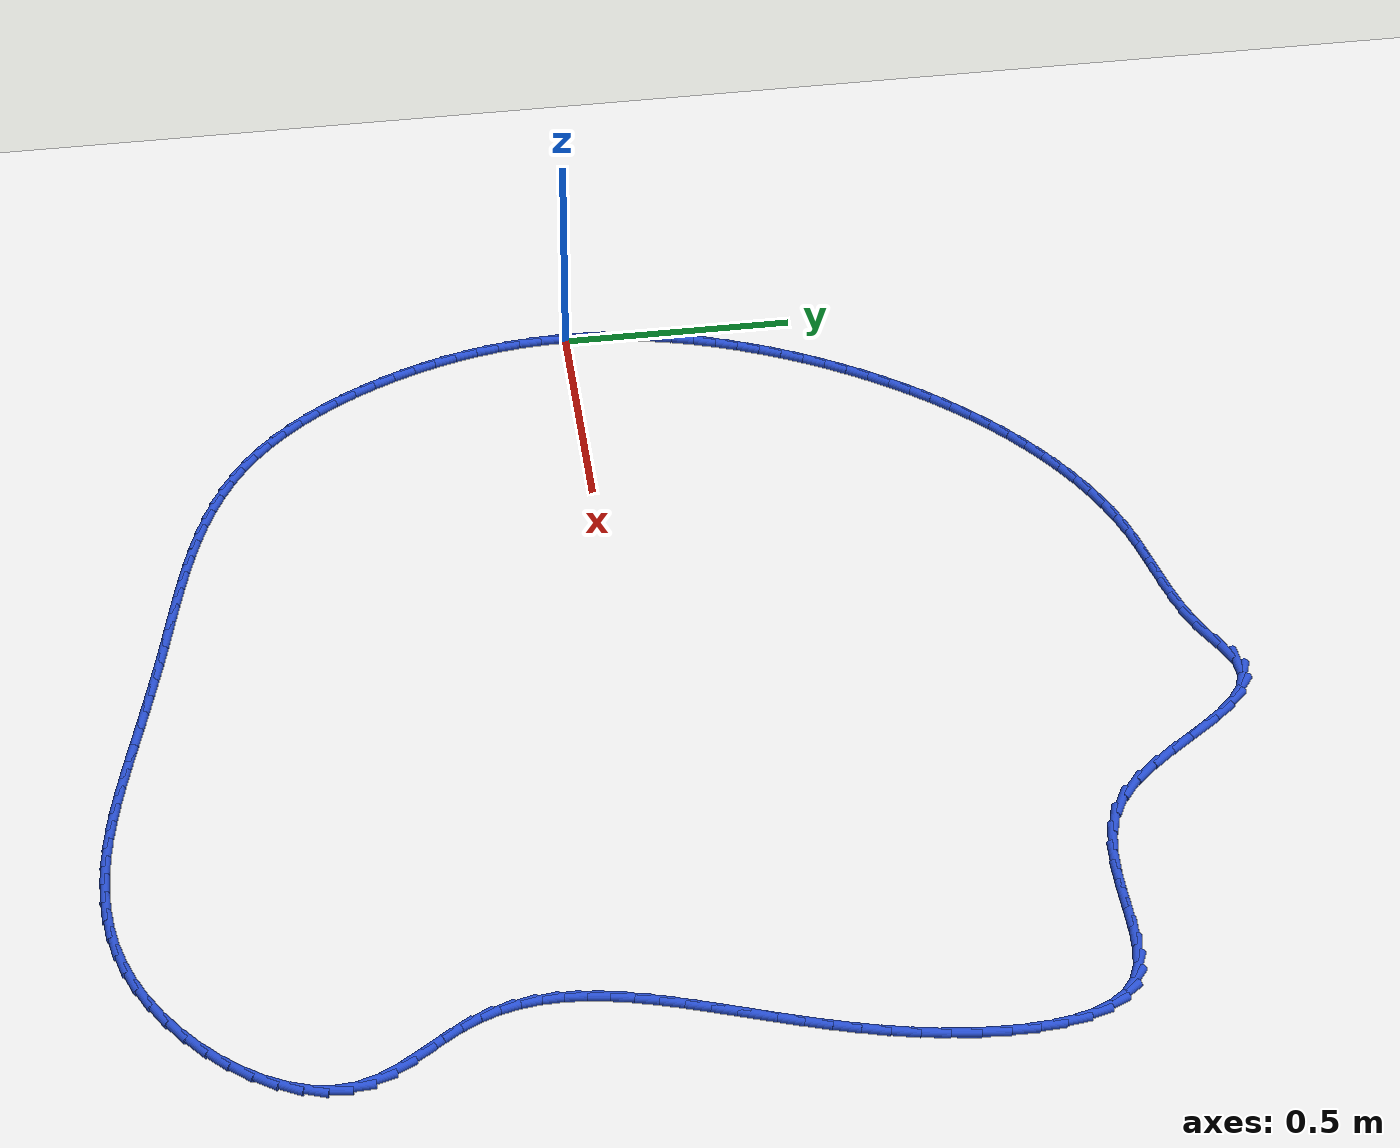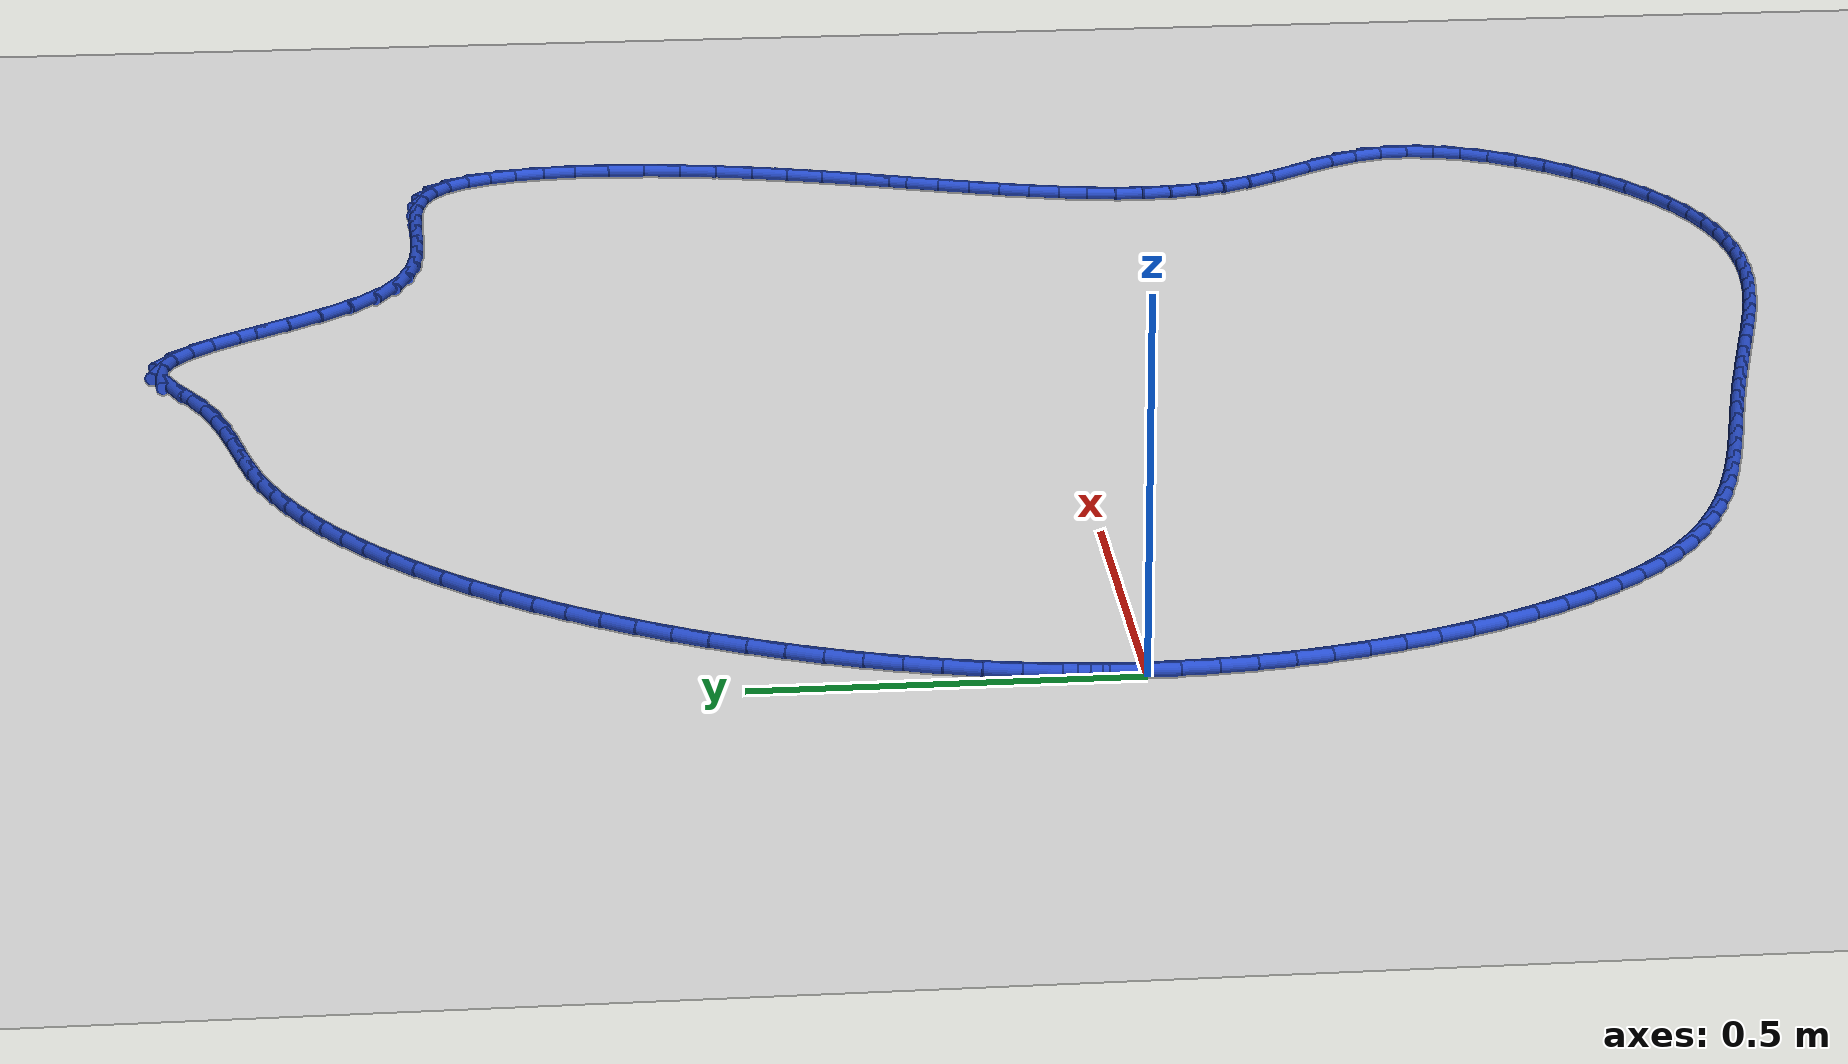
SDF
<sdf version="1.6">
 <world name="default">
  <light name="sun" type="directional">
   <pose>0 0 10 0 -0 0</pose>
   <diffuse>0.8 0.8 0.8 1</diffuse>
   <specular>0.2 0.2 0.2 1</specular>
   <attenuation>
    <range>1000</range>
    <constant>0.9</constant>
    <linear>0.01</linear>
    <quadratic>0.001</quadratic>
   </attenuation>
   <direction>-0.5 0.1 -0.9</direction>
  </light>
  <model name="ground_plane">
   <static>1</static>
   <link name="link">
    <collision name="collision">
     <geometry><plane><normal>0 0 1</normal><size>100 100</size></plane></geometry>
     <surface><friction><ode><mu>100</mu><mu2>50</mu2></ode></friction></surface>
    </collision>
    <visual name="visual">
     <cast_shadows>0</cast_shadows>
     <geometry><plane><normal>0 0 1</normal><size>100 100</size></plane></geometry>
     <material>
      <script><uri>file://media/materials/scripts/gazebo.material</uri><name>Gazebo/WhiteGlow</name></script>
     </material>
    </visual>
   </link>
  </model>
  <gravity>0 0 -9.8</gravity>
  <magnetic_field>6e-06 2.3e-05 -4.2e-05</magnetic_field>
  <atmosphere type="adiabatic"/>
  <physics name="default_physics" default="0" type="ode">
   <max_step_size>0.001</max_step_size>
   <real_time_factor>1</real_time_factor>
   <real_time_update_rate>1000</real_time_update_rate>
  </physics>
  <scene><ambient>0.4 0.4 0.4 1</ambient><background>0.7 0.7 0.7 1</background><shadows>1</shadows></scene>
  <spherical_coordinates>
   <surface_model>EARTH_WGS84</surface_model>
   <latitude_deg>0</latitude_deg>
   <longitude_deg>0</longitude_deg>
   <elevation>0</elevation>
   <heading_deg>0</heading_deg>
  </spherical_coordinates>
  <model name="line">
   <link name="link_0">
    <pose>4.163336342344337e-17 -4.163336342344337e-17 0.01 0 1.57 1.5400447321798174</pose>
    <collision name="collision">
     <geometry><cylinder><radius>0.01</radius><length>0.08</length></cylinder></geometry>
    </collision>
    <visual name="visual">
     <material>
      <script><name>Gazebo/Blue</name><uri>file://media/materials/scripts/gazebo.material</uri></script>
     </material>
     <geometry><cylinder><radius>0.01</radius><length>0.08</length></cylinder></geometry>
    </visual>
   </link>
   <link name="link_1">
    <pose>0.0015002505944763317 0.04877072796237831 0.01 0 1.57 1.4877429851813693</pose>
    <collision name="collision">
     <geometry><cylinder><radius>0.01</radius><length>0.08</length></cylinder></geometry>
    </collision>
    <visual name="visual">
     <material>
      <script><name>Gazebo/Blue</name><uri>file://media/materials/scripts/gazebo.material</uri></script>
     </material>
     <geometry><cylinder><radius>0.01</radius><length>0.08</length></cylinder></geometry>
    </visual>
   </link>
   <link name="link_2">
    <pose>0.005549995147745127 0.09741932740024425 0.01 0 1.57 1.437531070462646</pose>
    <collision name="collision">
     <geometry><cylinder><radius>0.01</radius><length>0.08</length></cylinder></geometry>
    </collision>
    <visual name="visual">
     <material>
      <script><name>Gazebo/Blue</name><uri>file://media/materials/scripts/gazebo.material</uri></script>
     </material>
     <geometry><cylinder><radius>0.01</radius><length>0.08</length></cylinder></geometry>
    </visual>
   </link>
   <link name="link_3">
    <pose>0.012051817081749808 0.14591873739414 0.01 0 1.57 1.3895318751148384</pose>
    <collision name="collision">
     <geometry><cylinder><radius>0.01</radius><length>0.08</length></cylinder></geometry>
    </collision>
    <visual name="visual">
     <material>
      <script><name>Gazebo/Blue</name><uri>file://media/materials/scripts/gazebo.material</uri></script>
     </material>
     <geometry><cylinder><radius>0.01</radius><length>0.08</length></cylinder></geometry>
    </visual>
   </link>
   <link name="link_4">
    <pose>0.02090829981843374 0.19424189702460748 0.01 0 1.57 1.3438170179797084</pose>
    <collision name="collision">
     <geometry><cylinder><radius>0.01</radius><length>0.08</length></cylinder></geometry>
    </collision>
    <visual name="visual">
     <material>
      <script><name>Gazebo/Blue</name><uri>file://media/materials/scripts/gazebo.material</uri></script>
     </material>
     <geometry><cylinder><radius>0.01</radius><length>0.08</length></cylinder></geometry>
    </visual>
   </link>
   <link name="link_5">
    <pose>0.032022026779740295 0.24236174537218888 0.01 0 1.57 1.3004132527795733</pose>
    <collision name="collision">
     <geometry><cylinder><radius>0.01</radius><length>0.08</length></cylinder></geometry>
    </collision>
    <visual name="visual">
     <material>
      <script><name>Gazebo/Blue</name><uri>file://media/materials/scripts/gazebo.material</uri></script>
     </material>
     <geometry><cylinder><radius>0.01</radius><length>0.08</length></cylinder></geometry>
    </visual>
   </link>
   <link name="link_6">
    <pose>0.04529558138761289 0.29025122151742644 0.01 0 1.57 1.2593097391518369</pose>
    <collision name="collision">
     <geometry><cylinder><radius>0.01</radius><length>0.08</length></cylinder></geometry>
    </collision>
    <visual name="visual">
     <material>
      <script><name>Gazebo/Blue</name><uri>file://media/materials/scripts/gazebo.material</uri></script>
     </material>
     <geometry><cylinder><radius>0.01</radius><length>0.08</length></cylinder></geometry>
    </visual>
   </link>
   <link name="link_7">
    <pose>0.06063154706399483 0.337883264540862 0.01 0 1.57 1.2204654533270505</pose>
    <collision name="collision">
     <geometry><cylinder><radius>0.01</radius><length>0.08</length></cylinder></geometry>
    </collision>
    <visual name="visual">
     <material>
      <script><name>Gazebo/Blue</name><uri>file://media/materials/scripts/gazebo.material</uri></script>
     </material>
     <geometry><cylinder><radius>0.01</radius><length>0.08</length></cylinder></geometry>
    </visual>
   </link>
   <link name="link_8">
    <pose>0.07793250723082955 0.3852308135230379 0.01 0 1.57 1.1837741862525684</pose>
    <collision name="collision">
     <geometry><cylinder><radius>0.01</radius><length>0.08</length></cylinder></geometry>
    </collision>
    <visual name="visual">
     <material>
      <script><name>Gazebo/Blue</name><uri>file://media/materials/scripts/gazebo.material</uri></script>
     </material>
     <geometry><cylinder><radius>0.01</radius><length>0.08</length></cylinder></geometry>
    </visual>
   </link>
   <link name="link_9">
    <pose>0.09710231904066233 0.4322642771726343 0.01 0 1.57 1.1483401596776046</pose>
    <collision name="collision">
     <geometry><cylinder><radius>0.01</radius><length>0.08</length></cylinder></geometry>
    </collision>
    <visual name="visual">
     <material>
      <script><name>Gazebo/Blue</name><uri>file://media/materials/scripts/gazebo.material</uri></script>
     </material>
     <geometry><cylinder><radius>0.01</radius><length>0.08</length></cylinder></geometry>
    </visual>
   </link>
   <link name="link_10">
    <pose>0.11806890477209978 0.47890625682230775 0.01 0 1.57 1.1132798120705825</pose>
    <collision name="collision">
     <geometry><cylinder><radius>0.01</radius><length>0.08</length></cylinder></geometry>
    </collision>
    <visual name="visual">
     <material>
      <script><name>Gazebo/Blue</name><uri>file://media/materials/scripts/gazebo.material</uri></script>
     </material>
     <geometry><cylinder><radius>0.01</radius><length>0.08</length></cylinder></geometry>
    </visual>
   </link>
   <link name="link_11">
    <pose>0.14078166126628136 0.5250366927987722 0.01 0 1.57 1.0783809923927883</pose>
    <collision name="collision">
     <geometry><cylinder><radius>0.01</radius><length>0.08</length></cylinder></geometry>
    </collision>
    <visual name="visual">
     <material>
      <script><name>Gazebo/Blue</name><uri>file://media/materials/scripts/gazebo.material</uri></script>
     </material>
     <geometry><cylinder><radius>0.01</radius><length>0.08</length></cylinder></geometry>
    </visual>
   </link>
   <link name="link_12">
    <pose>0.16519073887445251 0.5705340285181951 0.01 0 1.57 1.0434617121505405</pose>
    <collision name="collision">
     <geometry><cylinder><radius>0.01</radius><length>0.08</length></cylinder></geometry>
    </collision>
    <visual name="visual">
     <material>
      <script><name>Gazebo/Blue</name><uri>file://media/materials/scripts/gazebo.material</uri></script>
     </material>
     <geometry><cylinder><radius>0.01</radius><length>0.08</length></cylinder></geometry>
    </visual>
   </link>
   <link name="link_13">
    <pose>0.19124628794785878 0.6152767073967439 0.01 0 1.57 1.0083436608396281</pose>
    <collision name="collision">
     <geometry><cylinder><radius>0.01</radius><length>0.08</length></cylinder></geometry>
    </collision>
    <visual name="visual">
     <material>
      <script><name>Gazebo/Blue</name><uri>file://media/materials/scripts/gazebo.material</uri></script>
     </material>
     <geometry><cylinder><radius>0.01</radius><length>0.08</length></cylinder></geometry>
    </visual>
   </link>
   <link name="link_14">
    <pose>0.21889845883774575 0.6591431728505865 0.01 0 1.57 0.9728507419246204</pose>
    <collision name="collision">
     <geometry><cylinder><radius>0.01</radius><length>0.08</length></cylinder></geometry>
    </collision>
    <visual name="visual">
     <material>
      <script><name>Gazebo/Blue</name><uri>file://media/materials/scripts/gazebo.material</uri></script>
     </material>
     <geometry><cylinder><radius>0.01</radius><length>0.08</length></cylinder></geometry>
    </visual>
   </link>
   <link name="link_15">
    <pose>0.24809740189535898 0.7020118682958909 0.01 0 1.57 0.9368078074004589</pose>
    <collision name="collision">
     <geometry><cylinder><radius>0.01</radius><length>0.08</length></cylinder></geometry>
    </collision>
    <visual name="visual">
     <material>
      <script><name>Gazebo/Blue</name><uri>file://media/materials/scripts/gazebo.material</uri></script>
     </material>
     <geometry><cylinder><radius>0.01</radius><length>0.08</length></cylinder></geometry>
    </visual>
   </link>
   <link name="link_16">
    <pose>0.278793267471944 0.7437612371488239 0.01 0 1.57 0.9000396400433698</pose>
    <collision name="collision">
     <geometry><cylinder><radius>0.01</radius><length>0.08</length></cylinder></geometry>
    </collision>
    <visual name="visual">
     <material>
      <script><name>Gazebo/Blue</name><uri>file://media/materials/scripts/gazebo.material</uri></script>
     </material>
     <geometry><cylinder><radius>0.01</radius><length>0.08</length></cylinder></geometry>
    </visual>
   </link>
   <link name="link_17">
    <pose>0.31093620591874627 0.7842697228255541 0.01 0 1.57 0.8623702464824908</pose>
    <collision name="collision">
     <geometry><cylinder><radius>0.01</radius><length>0.08</length></cylinder></geometry>
    </collision>
    <visual name="visual">
     <material>
      <script><name>Gazebo/Blue</name><uri>file://media/materials/scripts/gazebo.material</uri></script>
     </material>
     <geometry><cylinder><radius>0.01</radius><length>0.08</length></cylinder></geometry>
    </visual>
   </link>
   <link name="link_18">
    <pose>0.3444763675870114 0.8234157687422484 0.01 0 1.57 0.8236225436384036</pose>
    <collision name="collision">
     <geometry><cylinder><radius>0.01</radius><length>0.08</length></cylinder></geometry>
    </collision>
    <visual name="visual">
     <material>
      <script><name>Gazebo/Blue</name><uri>file://media/materials/scripts/gazebo.material</uri></script>
     </material>
     <geometry><cylinder><radius>0.01</radius><length>0.08</length></cylinder></geometry>
    </visual>
   </link>
   <link name="link_19">
    <pose>0.37936390282798504 0.8610778183150752 0.01 0 1.57 0.7836185452450082</pose>
    <collision name="collision">
     <geometry><cylinder><radius>0.01</radius><length>0.08</length></cylinder></geometry>
    </collision>
    <visual name="visual">
     <material>
      <script><name>Gazebo/Blue</name><uri>file://media/materials/scripts/gazebo.material</uri></script>
     </material>
     <geometry><cylinder><radius>0.01</radius><length>0.08</length></cylinder></geometry>
    </visual>
   </link>
   <link name="link_20">
    <pose>0.4155489619929125 0.8971343149602017 0.01 0 1.57 0.7421801828797588</pose>
    <collision name="collision">
     <geometry><cylinder><radius>0.01</radius><length>0.08</length></cylinder></geometry>
    </collision>
    <visual name="visual">
     <material>
      <script><name>Gazebo/Blue</name><uri>file://media/materials/scripts/gazebo.material</uri></script>
     </material>
     <geometry><cylinder><radius>0.01</radius><length>0.08</length></cylinder></geometry>
    </visual>
   </link>
   <link name="link_21">
    <pose>0.45298169543303957 0.9314637020937956 0.01 0 1.57 0.699130924770832</pose>
    <collision name="collision">
     <geometry><cylinder><radius>0.01</radius><length>0.08</length></cylinder></geometry>
    </collision>
    <visual name="visual">
     <material>
      <script><name>Gazebo/Blue</name><uri>file://media/materials/scripts/gazebo.material</uri></script>
     </material>
     <geometry><cylinder><radius>0.01</radius><length>0.08</length></cylinder></geometry>
    </visual>
   </link>
   <link name="link_22">
    <pose>0.4916122534996117 0.9639444231320248 0.01 0 1.57 0.6542983812639901</pose>
    <collision name="collision">
     <geometry><cylinder><radius>0.01</radius><length>0.08</length></cylinder></geometry>
    </collision>
    <visual name="visual">
     <material>
      <script><name>Gazebo/Blue</name><uri>file://media/materials/scripts/gazebo.material</uri></script>
     </material>
     <geometry><cylinder><radius>0.01</radius><length>0.08</length></cylinder></geometry>
    </visual>
   </link>
   <link name="link_23">
    <pose>0.5313907865438745 0.9944549214910569 0.01 0 1.57 0.6075181009555289</pose>
    <collision name="collision">
     <geometry><cylinder><radius>0.01</radius><length>0.08</length></cylinder></geometry>
    </collision>
    <visual name="visual">
     <material>
      <script><name>Gazebo/Blue</name><uri>file://media/materials/scripts/gazebo.material</uri></script>
     </material>
     <geometry><cylinder><radius>0.01</radius><length>0.08</length></cylinder></geometry>
    </visual>
   </link>
   <link name="link_24">
    <pose>0.5722674449170732 1.0228736405870595 0.01 0 1.57 0.558638755063652</pose>
    <collision name="collision">
     <geometry><cylinder><radius>0.01</radius><length>0.08</length></cylinder></geometry>
    </collision>
    <visual name="visual">
     <material>
      <script><name>Gazebo/Blue</name><uri>file://media/materials/scripts/gazebo.material</uri></script>
     </material>
     <geometry><cylinder><radius>0.01</radius><length>0.08</length></cylinder></geometry>
    </visual>
   </link>
   <link name="link_25">
    <pose>0.6141923789704536 1.0490790238362 0.01 0 1.57 0.5075288642562584</pose>
    <collision name="collision">
     <geometry><cylinder><radius>0.01</radius><length>0.08</length></cylinder></geometry>
    </collision>
    <visual name="visual">
     <material>
      <script><name>Gazebo/Blue</name><uri>file://media/materials/scripts/gazebo.material</uri></script>
     </material>
     <geometry><cylinder><radius>0.01</radius><length>0.08</length></cylinder></geometry>
    </visual>
   </link>
   <link name="link_26">
    <pose>0.6571157390552613 1.0729495146546468 0.01 0 1.57 0.45408512290063396</pose>
    <collision name="collision">
     <geometry><cylinder><radius>0.01</radius><length>0.08</length></cylinder></geometry>
    </collision>
    <visual name="visual">
     <material>
      <script><name>Gazebo/Blue</name><uri>file://media/materials/scripts/gazebo.material</uri></script>
     </material>
     <geometry><cylinder><radius>0.01</radius><length>0.08</length></cylinder></geometry>
    </visual>
   </link>
   <link name="link_27">
    <pose>0.7009876755227419 1.094363556458567 0.01 0 1.57 0.39824220094327667</pose>
    <collision name="collision">
     <geometry><cylinder><radius>0.01</radius><length>0.08</length></cylinder></geometry>
    </collision>
    <visual name="visual">
     <material>
      <script><name>Gazebo/Blue</name><uri>file://media/materials/scripts/gazebo.material</uri></script>
     </material>
     <geometry><cylinder><radius>0.01</radius><length>0.08</length></cylinder></geometry>
    </visual>
   </link>
   <link name="link_28">
    <pose>0.7457583387241407 1.1131995926641285 0.01 0 1.57 0.33998938854565464</pose>
    <collision name="collision">
     <geometry><cylinder><radius>0.01</radius><length>0.08</length></cylinder></geometry>
    </collision>
    <visual name="visual">
     <material>
      <script><name>Gazebo/Blue</name><uri>file://media/materials/scripts/gazebo.material</uri></script>
     </material>
     <geometry><cylinder><radius>0.01</radius><length>0.08</length></cylinder></geometry>
    </visual>
   </link>
   <link name="link_29">
    <pose>0.7913778397790959 1.1293363478838214 0.01 0 1.57 0.2854719786690997</pose>
    <collision name="collision">
     <geometry><cylinder><radius>0.01</radius><length>0.08</length></cylinder></geometry>
    </collision>
    <visual name="visual">
     <material>
      <script><name>Gazebo/Blue</name><uri>file://media/materials/scripts/gazebo.material</uri></script>
     </material>
     <geometry><cylinder><radius>0.01</radius><length>0.08</length></cylinder></geometry>
    </visual>
   </link>
   <link name="link_30">
    <pose>0.8377551340123212 1.1429475348503093 0.01 0 1.57 0.2526227878856352</pose>
    <collision name="collision">
     <geometry><cylinder><radius>0.01</radius><length>0.08</length></cylinder></geometry>
    </collision>
    <visual name="visual">
     <material>
      <script><name>Gazebo/Blue</name><uri>file://media/materials/scripts/gazebo.material</uri></script>
     </material>
     <geometry><cylinder><radius>0.01</radius><length>0.08</length></cylinder></geometry>
    </visual>
   </link>
   <link name="link_31">
    <pose>0.884680063338611 1.1550606231230875 0.01 0 1.57 0.24469522103837837</pose>
    <collision name="collision">
     <geometry><cylinder><radius>0.01</radius><length>0.08</length></cylinder></geometry>
    </collision>
    <visual name="visual">
     <material>
      <script><name>Gazebo/Blue</name><uri>file://media/materials/scripts/gazebo.material</uri></script>
     </material>
     <geometry><cylinder><radius>0.01</radius><length>0.08</length></cylinder></geometry>
    </visual>
   </link>
   <link name="link_32">
    <pose>0.9319210454154752 1.1668566426871954 0.01 0 1.57 0.2613885659430776</pose>
    <collision name="collision">
     <geometry><cylinder><radius>0.01</radius><length>0.08</length></cylinder></geometry>
    </collision>
    <visual name="visual">
     <material>
      <script><name>Gazebo/Blue</name><uri>file://media/materials/scripts/gazebo.material</uri></script>
     </material>
     <geometry><cylinder><radius>0.01</radius><length>0.08</length></cylinder></geometry>
    </visual>
   </link>
   <link name="link_33">
    <pose>0.9792464979004245 1.179516623527674 0.01 0 1.57 0.3021458956083174</pose>
    <collision name="collision">
     <geometry><cylinder><radius>0.01</radius><length>0.08</length></cylinder></geometry>
    </collision>
    <visual name="visual">
     <material>
      <script><name>Gazebo/Blue</name><uri>file://media/materials/scripts/gazebo.material</uri></script>
     </material>
     <geometry><cylinder><radius>0.01</radius><length>0.08</length></cylinder></geometry>
    </visual>
   </link>
   <link name="link_34">
    <pose>1.0264248384509695 1.194221595629563 0.01 0 1.57 0.3658912367599728</pose>
    <collision name="collision">
     <geometry><cylinder><radius>0.01</radius><length>0.08</length></cylinder></geometry>
    </collision>
    <visual name="visual">
     <material>
      <script><name>Gazebo/Blue</name><uri>file://media/materials/scripts/gazebo.material</uri></script>
     </material>
     <geometry><cylinder><radius>0.01</radius><length>0.08</length></cylinder></geometry>
    </visual>
   </link>
   <link name="link_35">
    <pose>1.07322448472462 1.2121525889779026 0.01 0 1.57 0.45043373220248306</pose>
    <collision name="collision">
     <geometry><cylinder><radius>0.01</radius><length>0.08</length></cylinder></geometry>
    </collision>
    <visual name="visual">
     <material>
      <script><name>Gazebo/Blue</name><uri>file://media/materials/scripts/gazebo.material</uri></script>
     </material>
     <geometry><cylinder><radius>0.01</radius><length>0.08</length></cylinder></geometry>
    </visual>
   </link>
   <link name="link_36">
    <pose>1.1194137487499283 1.2344892606172977 0.01 0 1.57 0.5115273436337617</pose>
    <collision name="collision">
     <geometry><cylinder><radius>0.01</radius><length>0.08</length></cylinder></geometry>
    </collision>
    <visual name="visual">
     <material>
      <script><name>Gazebo/Blue</name><uri>file://media/materials/scripts/gazebo.material</uri></script>
     </material>
     <geometry><cylinder><radius>0.01</radius><length>0.08</length></cylinder></geometry>
    </visual>
   </link>
   <link name="link_37">
    <pose>1.1645626818131107 1.2598343209549603 0.01 0 1.57 0.4160245701209329</pose>
    <collision name="collision">
     <geometry><cylinder><radius>0.01</radius><length>0.08</length></cylinder></geometry>
    </collision>
    <visual name="visual">
     <material>
      <script><name>Gazebo/Blue</name><uri>file://media/materials/scripts/gazebo.material</uri></script>
     </material>
     <geometry><cylinder><radius>0.01</radius><length>0.08</length></cylinder></geometry>
    </visual>
   </link>
   <link name="link_38">
    <pose>1.207631395489441 1.2788626270640902 0.01 0 1.57 0.08881564727308935</pose>
    <collision name="collision">
     <geometry><cylinder><radius>0.01</radius><length>0.08</length></cylinder></geometry>
    </collision>
    <visual name="visual">
     <material>
      <script><name>Gazebo/Blue</name><uri>file://media/materials/scripts/gazebo.material</uri></script>
     </material>
     <geometry><cylinder><radius>0.01</radius><length>0.08</length></cylinder></geometry>
    </visual>
   </link>
   <link name="link_39">
    <pose>1.2477009795915115 1.2824308202798063 0.01 0 1.57 -0.31008215336885275</pose>
    <collision name="collision">
     <geometry><cylinder><radius>0.01</radius><length>0.08</length></cylinder></geometry>
    </collision>
    <visual name="visual">
     <material>
      <script><name>Gazebo/Blue</name><uri>file://media/materials/scripts/gazebo.material</uri></script>
     </material>
     <geometry><cylinder><radius>0.01</radius><length>0.08</length></cylinder></geometry>
    </visual>
   </link>
   <link name="link_40">
    <pose>1.285117404471107 1.2704419208641466 0.01 0 1.57 -0.6065291499646555</pose>
    <collision name="collision">
     <geometry><cylinder><radius>0.01</radius><length>0.08</length></cylinder></geometry>
    </collision>
    <visual name="visual">
     <material>
      <script><name>Gazebo/Blue</name><uri>file://media/materials/scripts/gazebo.material</uri></script>
     </material>
     <geometry><cylinder><radius>0.01</radius><length>0.08</length></cylinder></geometry>
    </visual>
   </link>
   <link name="link_41">
    <pose>1.3206453921466081 1.2457938455416242 0.01 0 1.57 -0.785439815209314</pose>
    <collision name="collision">
     <geometry><cylinder><radius>0.01</radius><length>0.08</length></cylinder></geometry>
    </collision>
    <visual name="visual">
     <material>
      <script><name>Gazebo/Blue</name><uri>file://media/materials/scripts/gazebo.material</uri></script>
     </material>
     <geometry><cylinder><radius>0.01</radius><length>0.08</length></cylinder></geometry>
    </visual>
   </link>
   <link name="link_42">
    <pose>1.3550499340037434 1.2113864375420977 0.01 0 1.57 -0.880983348141115</pose>
    <collision name="collision">
     <geometry><cylinder><radius>0.01</radius><length>0.08</length></cylinder></geometry>
    </collision>
    <visual name="visual">
     <material>
      <script><name>Gazebo/Blue</name><uri>file://media/materials/scripts/gazebo.material</uri></script>
     </material>
     <geometry><cylinder><radius>0.01</radius><length>0.08</length></cylinder></geometry>
    </visual>
   </link>
   <link name="link_43">
    <pose>1.3890960214282426 1.170119540095424 0.01 0 1.57 -0.9197992767301317</pose>
    <collision name="collision">
     <geometry><cylinder><radius>0.01</radius><length>0.08</length></cylinder></geometry>
    </collision>
    <visual name="visual">
     <material>
      <script><name>Gazebo/Blue</name><uri>file://media/materials/scripts/gazebo.material</uri></script>
     </material>
     <geometry><cylinder><radius>0.01</radius><length>0.08</length></cylinder></geometry>
    </visual>
   </link>
   <link name="link_44">
    <pose>1.423548645805835 1.1248929964314616 0.01 0 1.57 -0.9148391888629962</pose>
    <collision name="collision">
     <geometry><cylinder><radius>0.01</radius><length>0.08</length></cylinder></geometry>
    </collision>
    <visual name="visual">
     <material>
      <script><name>Gazebo/Blue</name><uri>file://media/materials/scripts/gazebo.material</uri></script>
     </material>
     <geometry><cylinder><radius>0.01</radius><length>0.08</length></cylinder></geometry>
    </visual>
   </link>
   <link name="link_45">
    <pose>1.4591727985222502 1.0786066497800673 0.01 0 1.57 -0.8691656797073278</pose>
    <collision name="collision">
     <geometry><cylinder><radius>0.01</radius><length>0.08</length></cylinder></geometry>
    </collision>
    <visual name="visual">
     <material>
      <script><name>Gazebo/Blue</name><uri>file://media/materials/scripts/gazebo.material</uri></script>
     </material>
     <geometry><cylinder><radius>0.01</radius><length>0.08</length></cylinder></geometry>
    </visual>
   </link>
   <link name="link_46">
    <pose>1.4967334709632174 1.0341603433711002 0.01 0 1.57 -0.7784485403927817</pose>
    <collision name="collision">
     <geometry><cylinder><radius>0.01</radius><length>0.08</length></cylinder></geometry>
    </collision>
    <visual name="visual">
     <material>
      <script><name>Gazebo/Blue</name><uri>file://media/materials/scripts/gazebo.material</uri></script>
     </material>
     <geometry><cylinder><radius>0.01</radius><length>0.08</length></cylinder></geometry>
    </visual>
   </link>
   <link name="link_47">
    <pose>1.5369956545144663 0.994453920434418 0.01 0 1.57 -0.6327338617281203</pose>
    <collision name="collision">
     <geometry><cylinder><radius>0.01</radius><length>0.08</length></cylinder></geometry>
    </collision>
    <visual name="visual">
     <material>
      <script><name>Gazebo/Blue</name><uri>file://media/materials/scripts/gazebo.material</uri></script>
     </material>
     <geometry><cylinder><radius>0.01</radius><length>0.08</length></cylinder></geometry>
    </visual>
   </link>
   <link name="link_48">
    <pose>1.5807243405617257 0.9623872241998779 0.01 0 1.57 -0.4365214389359449</pose>
    <collision name="collision">
     <geometry><cylinder><radius>0.01</radius><length>0.08</length></cylinder></geometry>
    </collision>
    <visual name="visual">
     <material>
      <script><name>Gazebo/Blue</name><uri>file://media/materials/scripts/gazebo.material</uri></script>
     </material>
     <geometry><cylinder><radius>0.01</radius><length>0.08</length></cylinder></geometry>
    </visual>
   </link>
   <link name="link_49">
    <pose>1.6284111466724007 0.9401395204610673 0.01 0 1.57 -0.25900743046637276</pose>
    <collision name="collision">
     <geometry><cylinder><radius>0.01</radius><length>0.08</length></cylinder></geometry>
    </collision>
    <visual name="visual">
     <material>
      <script><name>Gazebo/Blue</name><uri>file://media/materials/scripts/gazebo.material</uri></script>
     </material>
     <geometry><cylinder><radius>0.01</radius><length>0.08</length></cylinder></geometry>
    </visual>
   </link>
   <link name="link_50">
    <pose>1.679318868088891 0.9266510609537888 0.01 0 1.57 -0.12561458461229144</pose>
    <collision name="collision">
     <geometry><cylinder><radius>0.01</radius><length>0.08</length></cylinder></geometry>
    </collision>
    <visual name="visual">
     <material>
      <script><name>Gazebo/Blue</name><uri>file://media/materials/scripts/gazebo.material</uri></script>
     </material>
     <geometry><cylinder><radius>0.01</radius><length>0.08</length></cylinder></geometry>
    </visual>
   </link>
   <link name="link_51">
    <pose>1.732365177932654 0.919952400886823 0.01 0 1.57 -0.0347044411926686</pose>
    <collision name="collision">
     <geometry><cylinder><radius>0.01</radius><length>0.08</length></cylinder></geometry>
    </collision>
    <visual name="visual">
     <material>
      <script><name>Gazebo/Blue</name><uri>file://media/materials/scripts/gazebo.material</uri></script>
     </material>
     <geometry><cylinder><radius>0.01</radius><length>0.08</length></cylinder></geometry>
    </visual>
   </link>
   <link name="link_52">
    <pose>1.7864677312597443 0.9180740478509248 0.01 0 1.57 0.017981149726221397</pose>
    <collision name="collision">
     <geometry><cylinder><radius>0.01</radius><length>0.08</length></cylinder></geometry>
    </collision>
    <visual name="visual">
     <material>
      <script><name>Gazebo/Blue</name><uri>file://media/materials/scripts/gazebo.material</uri></script>
     </material>
     <geometry><cylinder><radius>0.01</radius><length>0.08</length></cylinder></geometry>
    </visual>
   </link>
   <link name="link_53">
    <pose>1.8405441831262175 0.9190465094368503 0.01 0 1.57 0.03498390122692101</pose>
    <collision name="collision">
     <geometry><cylinder><radius>0.01</radius><length>0.08</length></cylinder></geometry>
    </collision>
    <visual name="visual">
     <material>
      <script><name>Gazebo/Blue</name><uri>file://media/materials/scripts/gazebo.material</uri></script>
     </material>
     <geometry><cylinder><radius>0.01</radius><length>0.08</length></cylinder></geometry>
    </visual>
   </link>
   <link name="link_54">
    <pose>1.893512188588129 0.920900293235355 0.01 0 1.57 0.015076754488411427</pose>
    <collision name="collision">
     <geometry><cylinder><radius>0.01</radius><length>0.08</length></cylinder></geometry>
    </collision>
    <visual name="visual">
     <material>
      <script><name>Gazebo/Blue</name><uri>file://media/materials/scripts/gazebo.material</uri></script>
     </material>
     <geometry><cylinder><radius>0.01</radius><length>0.08</length></cylinder></geometry>
    </visual>
   </link>
   <link name="link_55">
    <pose>1.9442894027015325 0.9216659068371938 0.01 0 1.57 -0.04821213139926054</pose>
    <collision name="collision">
     <geometry><cylinder><radius>0.01</radius><length>0.08</length></cylinder></geometry>
    </collision>
    <visual name="visual">
     <material>
      <script><name>Gazebo/Blue</name><uri>file://media/materials/scripts/gazebo.material</uri></script>
     </material>
     <geometry><cylinder><radius>0.01</radius><length>0.08</length></cylinder></geometry>
    </visual>
   </link>
   <link name="link_56">
    <pose>1.9917934805224833 0.9193738578331223 0.01 0 1.57 -0.16802844585005158</pose>
    <collision name="collision">
     <geometry><cylinder><radius>0.01</radius><length>0.08</length></cylinder></geometry>
    </collision>
    <visual name="visual">
     <material>
      <script><name>Gazebo/Blue</name><uri>file://media/materials/scripts/gazebo.material</uri></script>
     </material>
     <geometry><cylinder><radius>0.01</radius><length>0.08</length></cylinder></geometry>
    </visual>
   </link>
   <link name="link_57">
    <pose>2.0349420771070372 0.9120546538138964 0.01 0 1.57 -0.36281697408463104</pose>
    <collision name="collision">
     <geometry><cylinder><radius>0.01</radius><length>0.08</length></cylinder></geometry>
    </collision>
    <visual name="visual">
     <material>
      <script><name>Gazebo/Blue</name><uri>file://media/materials/scripts/gazebo.material</uri></script>
     </material>
     <geometry><cylinder><radius>0.01</radius><length>0.08</length></cylinder></geometry>
    </visual>
   </link>
   <link name="link_58">
    <pose>2.07265284751125 0.8977388023702713 0.01 0 1.57 -0.6368235792398497</pose>
    <collision name="collision">
     <geometry><cylinder><radius>0.01</radius><length>0.08</length></cylinder></geometry>
    </collision>
    <visual name="visual">
     <material>
      <script><name>Gazebo/Blue</name><uri>file://media/materials/scripts/gazebo.material</uri></script>
     </material>
     <geometry><cylinder><radius>0.01</radius><length>0.08</length></cylinder></geometry>
    </visual>
   </link>
   <link name="link_59">
    <pose>2.1039195191354865 0.8746134030038326 0.01 0 1.57 -0.9121560732776308</pose>
    <collision name="collision">
     <geometry><cylinder><radius>0.01</radius><length>0.08</length></cylinder></geometry>
    </collision>
    <visual name="visual">
     <material>
      <script><name>Gazebo/Blue</name><uri>file://media/materials/scripts/gazebo.material</uri></script>
     </material>
     <geometry><cylinder><radius>0.01</radius><length>0.08</length></cylinder></geometry>
    </visual>
   </link>
   <link name="link_60">
    <pose>2.12862360534909 0.8426930275064987 0.01 0 1.57 -1.1309427596672432</pose>
    <collision name="collision">
     <geometry><cylinder><radius>0.01</radius><length>0.08</length></cylinder></geometry>
    </collision>
    <visual name="visual">
     <material>
      <script><name>Gazebo/Blue</name><uri>file://media/materials/scripts/gazebo.material</uri></script>
     </material>
     <geometry><cylinder><radius>0.01</radius><length>0.08</length></cylinder></geometry>
    </visual>
   </link>
   <link name="link_61">
    <pose>2.1472210247209413 0.8031746380460922 0.01 0 1.57 -1.2956789865632539</pose>
    <collision name="collision">
     <geometry><cylinder><radius>0.01</radius><length>0.08</length></cylinder></geometry>
    </collision>
    <visual name="visual">
     <material>
      <script><name>Gazebo/Blue</name><uri>file://media/materials/scripts/gazebo.material</uri></script>
     </material>
     <geometry><cylinder><radius>0.01</radius><length>0.08</length></cylinder></geometry>
    </visual>
   </link>
   <link name="link_62">
    <pose>2.1601773431941163 0.7572750555285007 0.01 0 1.57 -1.4195861109109122</pose>
    <collision name="collision">
     <geometry><cylinder><radius>0.01</radius><length>0.08</length></cylinder></geometry>
    </collision>
    <visual name="visual">
     <material>
      <script><name>Gazebo/Blue</name><uri>file://media/materials/scripts/gazebo.material</uri></script>
     </material>
     <geometry><cylinder><radius>0.01</radius><length>0.08</length></cylinder></geometry>
    </visual>
   </link>
   <link name="link_63">
    <pose>2.1679581267116914 0.7062111008596129 0.01 0 1.57 -1.5150328854573967</pose>
    <collision name="collision">
     <geometry><cylinder><radius>0.01</radius><length>0.08</length></cylinder></geometry>
    </collision>
    <visual name="visual">
     <material>
      <script><name>Gazebo/Blue</name><uri>file://media/materials/scripts/gazebo.material</uri></script>
     </material>
     <geometry><cylinder><radius>0.01</radius><length>0.08</length></cylinder></geometry>
    </visual>
   </link>
   <link name="link_64">
    <pose>2.1710289412167407 0.6511995949453165 0.01 0 1.57 1.5504745124456742</pose>
    <collision name="collision">
     <geometry><cylinder><radius>0.01</radius><length>0.08</length></cylinder></geometry>
    </collision>
    <visual name="visual">
     <material>
      <script><name>Gazebo/Blue</name><uri>file://media/materials/scripts/gazebo.material</uri></script>
     </material>
     <geometry><cylinder><radius>0.01</radius><length>0.08</length></cylinder></geometry>
    </visual>
   </link>
   <link name="link_65">
    <pose>2.1698553526523425 0.5934573586915 0.01 0 1.57 1.4874135358619225</pose>
    <collision name="collision">
     <geometry><cylinder><radius>0.01</radius><length>0.08</length></cylinder></geometry>
    </collision>
    <visual name="visual">
     <material>
      <script><name>Gazebo/Blue</name><uri>file://media/materials/scripts/gazebo.material</uri></script>
     </material>
     <geometry><cylinder><radius>0.01</radius><length>0.08</length></cylinder></geometry>
    </visual>
   </link>
   <link name="link_66">
    <pose>2.1649029269615716 0.5342012130040507 0.01 0 1.57 1.4328823219346558</pose>
    <collision name="collision">
     <geometry><cylinder><radius>0.01</radius><length>0.08</length></cylinder></geometry>
    </collision>
    <visual name="visual">
     <material>
      <script><name>Gazebo/Blue</name><uri>file://media/materials/scripts/gazebo.material</uri></script>
     </material>
     <geometry><cylinder><radius>0.01</radius><length>0.08</length></cylinder></geometry>
    </visual>
   </link>
   <link name="link_67">
    <pose>2.156637230087503 0.47464797878885645 0.01 0 1.57 1.3835996386988472</pose>
    <collision name="collision">
     <geometry><cylinder><radius>0.01</radius><length>0.08</length></cylinder></geometry>
    </collision>
    <visual name="visual">
     <material>
      <script><name>Gazebo/Blue</name><uri>file://media/materials/scripts/gazebo.material</uri></script>
     </material>
     <geometry><cylinder><radius>0.01</radius><length>0.08</length></cylinder></geometry>
    </visual>
   </link>
   <link name="link_68">
    <pose>2.1455248128868356 0.41598075346847907 0.01 0 1.57 1.3396217985513634</pose>
    <collision name="collision">
     <geometry><cylinder><radius>0.01</radius><length>0.08</length></cylinder></geometry>
    </collision>
    <visual name="visual">
     <material>
      <script><name>Gazebo/Blue</name><uri>file://media/materials/scripts/gazebo.material</uri></script>
     </material>
     <geometry><cylinder><radius>0.01</radius><length>0.08</length></cylinder></geometry>
    </visual>
   </link>
   <link name="link_69">
    <pose>2.132051032192797 0.35873871704708843 0.01 0 1.57 1.30288761015329</pose>
    <collision name="collision">
     <geometry><cylinder><radius>0.01</radius><length>0.08</length></cylinder></geometry>
    </collision>
    <visual name="visual">
     <material>
      <script><name>Gazebo/Blue</name><uri>file://media/materials/scripts/gazebo.material</uri></script>
     </material>
     <geometry><cylinder><radius>0.01</radius><length>0.08</length></cylinder></geometry>
    </visual>
   </link>
   <link name="link_70">
    <pose>2.116718133414907 0.30288278397451507 0.01 0 1.57 1.2737911479376993</pose>
    <collision name="collision">
     <geometry><cylinder><radius>0.01</radius><length>0.08</length></cylinder></geometry>
    </collision>
    <visual name="visual">
     <material>
      <script><name>Gazebo/Blue</name><uri>file://media/materials/scripts/gazebo.material</uri></script>
     </material>
     <geometry><cylinder><radius>0.01</radius><length>0.08</length></cylinder></geometry>
    </visual>
   </link>
   <link name="link_71">
    <pose>2.1000289620055455 0.24835332320812104 0.01 0 1.57 1.2526256482752431</pose>
    <collision name="collision">
     <geometry><cylinder><radius>0.01</radius><length>0.08</length></cylinder></geometry>
    </collision>
    <visual name="visual">
     <material>
      <script><name>Gazebo/Blue</name><uri>file://media/materials/scripts/gazebo.material</uri></script>
     </material>
     <geometry><cylinder><radius>0.01</radius><length>0.08</length></cylinder></geometry>
    </visual>
   </link>
   <link name="link_72">
    <pose>2.082486363417089 0.19509070370526924 0.01 0 1.57 1.239715138979703</pose>
    <collision name="collision">
     <geometry><cylinder><radius>0.01</radius><length>0.08</length></cylinder></geometry>
    </collision>
    <visual name="visual">
     <material>
      <script><name>Gazebo/Blue</name><uri>file://media/materials/scripts/gazebo.material</uri></script>
     </material>
     <geometry><cylinder><radius>0.01</radius><length>0.08</length></cylinder></geometry>
    </visual>
   </link>
   <link name="link_73">
    <pose>2.0645931831019184 0.1430352944233217 0.01 0 1.57 1.2354665307370736</pose>
    <collision name="collision">
     <geometry><cylinder><radius>0.01</radius><length>0.08</length></cylinder></geometry>
    </collision>
    <visual name="visual">
     <material>
      <script><name>Gazebo/Blue</name><uri>file://media/materials/scripts/gazebo.material</uri></script>
     </material>
     <geometry><cylinder><radius>0.01</radius><length>0.08</length></cylinder></geometry>
    </visual>
   </link>
   <link name="link_74">
    <pose>2.0468522665124116 0.0921274643196405 0.01 0 1.57 1.240414467616866</pose>
    <collision name="collision">
     <geometry><cylinder><radius>0.01</radius><length>0.08</length></cylinder></geometry>
    </collision>
    <visual name="visual">
     <material>
      <script><name>Gazebo/Blue</name><uri>file://media/materials/scripts/gazebo.material</uri></script>
     </material>
     <geometry><cylinder><radius>0.01</radius><length>0.08</length></cylinder></geometry>
    </visual>
   </link>
   <link name="link_75">
    <pose>2.029766459100948 0.04230758235158808 0.01 0 1.57 1.2552563561996182</pose>
    <collision name="collision">
     <geometry><cylinder><radius>0.01</radius><length>0.08</length></cylinder></geometry>
    </collision>
    <visual name="visual">
     <material>
      <script><name>Gazebo/Blue</name><uri>file://media/materials/scripts/gazebo.material</uri></script>
     </material>
     <geometry><cylinder><radius>0.01</radius><length>0.08</length></cylinder></geometry>
    </visual>
   </link>
   <link name="link_76">
    <pose>2.0138386063199047 -0.006483982523473847 0.01 0 1.57 1.2808713230961957</pose>
    <collision name="collision">
     <geometry><cylinder><radius>0.01</radius><length>0.08</length></cylinder></geometry>
    </collision>
    <visual name="visual">
     <material>
      <script><name>Gazebo/Blue</name><uri>file://media/materials/scripts/gazebo.material</uri></script>
     </material>
     <geometry><cylinder><radius>0.01</radius><length>0.08</length></cylinder></geometry>
    </visual>
   </link>
   <link name="link_77">
    <pose>1.999571553621662 -0.054306861348182627 0.01 0 1.57 1.3183097221567153</pose>
    <collision name="collision">
     <geometry><cylinder><radius>0.01</radius><length>0.08</length></cylinder></geometry>
    </collision>
    <visual name="visual">
     <material>
      <script><name>Gazebo/Blue</name><uri>file://media/materials/scripts/gazebo.material</uri></script>
     </material>
     <geometry><cylinder><radius>0.01</radius><length>0.08</length></cylinder></geometry>
    </visual>
   </link>
   <link name="link_78">
    <pose>1.9874681464585988 -0.1012206851651751 0.01 0 1.57 1.3687286867723003</pose>
    <collision name="collision">
     <geometry><cylinder><radius>0.01</radius><length>0.08</length></cylinder></geometry>
    </collision>
    <visual name="visual">
     <material>
      <script><name>Gazebo/Blue</name><uri>file://media/materials/scripts/gazebo.material</uri></script>
     </material>
     <geometry><cylinder><radius>0.01</radius><length>0.08</length></cylinder></geometry>
    </visual>
   </link>
   <link name="link_79">
    <pose>1.9780312302830938 -0.14728508501709073 0.01 0 1.57 1.4332358566750991</pose>
    <collision name="collision">
     <geometry><cylinder><radius>0.01</radius><length>0.08</length></cylinder></geometry>
    </collision>
    <visual name="visual">
     <material>
      <script><name>Gazebo/Blue</name><uri>file://media/materials/scripts/gazebo.material</uri></script>
     </material>
     <geometry><cylinder><radius>0.01</radius><length>0.08</length></cylinder></geometry>
    </visual>
   </link>
   <link name="link_80">
    <pose>1.9717636505475253 -0.19255969194656558 0.01 0 1.57 1.51259677325692</pose>
    <collision name="collision">
     <geometry><cylinder><radius>0.01</radius><length>0.08</length></cylinder></geometry>
    </collision>
    <visual name="visual">
     <material>
      <script><name>Gazebo/Blue</name><uri>file://media/materials/scripts/gazebo.material</uri></script>
     </material>
     <geometry><cylinder><radius>0.01</radius><length>0.08</length></cylinder></geometry>
    </visual>
   </link>
   <link name="link_81">
    <pose>1.9691682527042726 -0.23710413699623897 0.01 0 1.57 -1.5348080290894706</pose>
    <collision name="collision">
     <geometry><cylinder><radius>0.01</radius><length>0.08</length></cylinder></geometry>
    </collision>
    <visual name="visual">
     <material>
      <script><name>Gazebo/Blue</name><uri>file://media/materials/scripts/gazebo.material</uri></script>
     </material>
     <geometry><cylinder><radius>0.01</radius><length>0.08</length></cylinder></geometry>
    </visual>
   </link>
   <link name="link_82">
    <pose>1.9707478822057145 -0.28097805120874786 0.01 0 1.57 -1.4271538708264282</pose>
    <collision name="collision">
     <geometry><cylinder><radius>0.01</radius><length>0.08</length></cylinder></geometry>
    </collision>
    <visual name="visual">
     <material>
      <script><name>Gazebo/Blue</name><uri>file://media/materials/scripts/gazebo.material</uri></script>
     </material>
     <geometry><cylinder><radius>0.01</radius><length>0.08</length></cylinder></geometry>
    </visual>
   </link>
   <link name="link_83">
    <pose>1.9770053845042295 -0.3242410656267294 0.01 0 1.57 -1.3091358136497435</pose>
    <collision name="collision">
     <geometry><cylinder><radius>0.01</radius><length>0.08</length></cylinder></geometry>
    </collision>
    <visual name="visual">
     <material>
      <script><name>Gazebo/Blue</name><uri>file://media/materials/scripts/gazebo.material</uri></script>
     </material>
     <geometry><cylinder><radius>0.01</radius><length>0.08</length></cylinder></geometry>
    </visual>
   </link>
   <link name="link_84">
    <pose>1.9884436050521967 -0.36695281129282253 0.01 0 1.57 -1.1855264503517295</pose>
    <collision name="collision">
     <geometry><cylinder><radius>0.01</radius><length>0.08</length></cylinder></geometry>
    </collision>
    <visual name="visual">
     <material>
      <script><name>Gazebo/Blue</name><uri>file://media/materials/scripts/gazebo.material</uri></script>
     </material>
     <geometry><cylinder><radius>0.01</radius><length>0.08</length></cylinder></geometry>
    </visual>
   </link>
   <link name="link_85">
    <pose>2.005565389301995 -0.4091729192496638 0.01 0 1.57 -1.062921221758552</pose>
    <collision name="collision">
     <geometry><cylinder><radius>0.01</radius><length>0.08</length></cylinder></geometry>
    </collision>
    <visual name="visual">
     <material>
      <script><name>Gazebo/Blue</name><uri>file://media/materials/scripts/gazebo.material</uri></script>
     </material>
     <geometry><cylinder><radius>0.01</radius><length>0.08</length></cylinder></geometry>
    </visual>
   </link>
   <link name="link_86">
    <pose>2.0288254391963587 -0.4509645255753192 0.01 0 1.57 -0.9749347400510502</pose>
    <collision name="collision">
     <geometry><cylinder><radius>0.01</radius><length>0.08</length></cylinder></geometry>
    </collision>
    <visual name="visual">
     <material>
      <script><name>Gazebo/Blue</name><uri>file://media/materials/scripts/gazebo.material</uri></script>
     </material>
     <geometry><cylinder><radius>0.01</radius><length>0.08</length></cylinder></geometry>
    </visual>
   </link>
   <link name="link_87">
    <pose>2.056998613192884 -0.49251306551072077 0.01 0 1.57 -0.9499197458881184</pose>
    <collision name="collision">
     <geometry><cylinder><radius>0.01</radius><length>0.08</length></cylinder></geometry>
    </collision>
    <visual name="visual">
     <material>
      <script><name>Gazebo/Blue</name><uri>file://media/materials/scripts/gazebo.material</uri></script>
     </material>
     <geometry><cylinder><radius>0.01</radius><length>0.08</length></cylinder></geometry>
    </visual>
   </link>
   <link name="link_88">
    <pose>2.086782457167427 -0.5341552107613947 0.01 0 1.57 -0.9842961640721551</pose>
    <collision name="collision">
     <geometry><cylinder><radius>0.01</radius><length>0.08</length></cylinder></geometry>
    </collision>
    <visual name="visual">
     <material>
      <script><name>Gazebo/Blue</name><uri>file://media/materials/scripts/gazebo.material</uri></script>
     </material>
     <geometry><cylinder><radius>0.01</radius><length>0.08</length></cylinder></geometry>
    </visual>
   </link>
   <link name="link_89">
    <pose>2.1147457540352805 -0.5762370074790149 0.01 0 1.57 -1.0835878134169386</pose>
    <collision name="collision">
     <geometry><cylinder><radius>0.01</radius><length>0.08</length></cylinder></geometry>
    </collision>
    <visual name="visual">
     <material>
      <script><name>Gazebo/Blue</name><uri>file://media/materials/scripts/gazebo.material</uri></script>
     </material>
     <geometry><cylinder><radius>0.01</radius><length>0.08</length></cylinder></geometry>
    </visual>
   </link>
   <link name="link_90">
    <pose>2.137457286711737 -0.6191045018152529 0.01 0 1.57 -1.262056328636429</pose>
    <collision name="collision">
     <geometry><cylinder><radius>0.01</radius><length>0.08</length></cylinder></geometry>
    </collision>
    <visual name="visual">
     <material>
      <script><name>Gazebo/Blue</name><uri>file://media/materials/scripts/gazebo.material</uri></script>
     </material>
     <geometry><cylinder><radius>0.01</radius><length>0.08</length></cylinder></geometry>
    </visual>
   </link>
   <link name="link_91">
    <pose>2.151490046479375 -0.6631027889027866 0.01 0 1.57 -1.5013290513289506</pose>
    <collision name="collision">
     <geometry><cylinder><radius>0.01</radius><length>0.08</length></cylinder></geometry>
    </collision>
    <visual name="visual">
     <material>
      <script><name>Gazebo/Blue</name><uri>file://media/materials/scripts/gazebo.material</uri></script>
     </material>
     <geometry><cylinder><radius>0.01</radius><length>0.08</length></cylinder></geometry>
    </visual>
   </link>
   <link name="link_92">
    <pose>2.154634954376019 -0.7083017325905194 0.01 0 1.57 1.4180276969786763</pose>
    <collision name="collision">
     <geometry><cylinder><radius>0.01</radius><length>0.08</length></cylinder></geometry>
    </collision>
    <visual name="visual">
     <material>
      <script><name>Gazebo/Blue</name><uri>file://media/materials/scripts/gazebo.material</uri></script>
     </material>
     <geometry><cylinder><radius>0.01</radius><length>0.08</length></cylinder></geometry>
    </visual>
   </link>
   <link name="link_93">
    <pose>2.1475809656261275 -0.7541162905916041 0.01 0 1.57 1.2315972203387082</pose>
    <collision name="collision">
     <geometry><cylinder><radius>0.01</radius><length>0.08</length></cylinder></geometry>
    </collision>
    <visual name="visual">
     <material>
      <script><name>Gazebo/Blue</name><uri>file://media/materials/scripts/gazebo.material</uri></script>
     </material>
     <geometry><cylinder><radius>0.01</radius><length>0.08</length></cylinder></geometry>
    </visual>
   </link>
   <link name="link_94">
    <pose>2.131438779992775 -0.7998661135702579 0.01 0 1.57 1.0788144934448627</pose>
    <collision name="collision">
     <geometry><cylinder><radius>0.01</radius><length>0.08</length></cylinder></geometry>
    </collision>
    <visual name="visual">
     <material>
      <script><name>Gazebo/Blue</name><uri>file://media/materials/scripts/gazebo.material</uri></script>
     </material>
     <geometry><cylinder><radius>0.01</radius><length>0.08</length></cylinder></geometry>
    </visual>
   </link>
   <link name="link_95">
    <pose>2.107319097239034 -0.844870852190695 0.01 0 1.57 0.952701599898569</pose>
    <collision name="collision">
     <geometry><cylinder><radius>0.01</radius><length>0.08</length></cylinder></geometry>
    </collision>
    <visual name="visual">
     <material>
      <script><name>Gazebo/Blue</name><uri>file://media/materials/scripts/gazebo.material</uri></script>
     </material>
     <geometry><cylinder><radius>0.01</radius><length>0.08</length></cylinder></geometry>
    </visual>
   </link>
   <link name="link_96">
    <pose>2.0763326171279792 -0.8884501571171297 0.01 0 1.57 0.8458101176707273</pose>
    <collision name="collision">
     <geometry><cylinder><radius>0.01</radius><length>0.08</length></cylinder></geometry>
    </collision>
    <visual name="visual">
     <material>
      <script><name>Gazebo/Blue</name><uri>file://media/materials/scripts/gazebo.material</uri></script>
     </material>
     <geometry><cylinder><radius>0.01</radius><length>0.08</length></cylinder></geometry>
    </visual>
   </link>
   <link name="link_97">
    <pose>2.0395900394226834 -0.9299236790137784 0.01 0 1.57 0.751685387845838</pose>
    <collision name="collision">
     <geometry><cylinder><radius>0.01</radius><length>0.08</length></cylinder></geometry>
    </collision>
    <visual name="visual">
     <material>
      <script><name>Gazebo/Blue</name><uri>file://media/materials/scripts/gazebo.material</uri></script>
     </material>
     <geometry><cylinder><radius>0.01</radius><length>0.08</length></cylinder></geometry>
    </visual>
   </link>
   <link name="link_98">
    <pose>1.9982020638862208 -0.9686110685448553 0.01 0 1.57 0.6649295341870509</pose>
    <collision name="collision">
     <geometry><cylinder><radius>0.01</radius><length>0.08</length></cylinder></geometry>
    </collision>
    <visual name="visual">
     <material>
      <script><name>Gazebo/Blue</name><uri>file://media/materials/scripts/gazebo.material</uri></script>
     </material>
     <geometry><cylinder><radius>0.01</radius><length>0.08</length></cylinder></geometry>
    </visual>
   </link>
   <link name="link_99">
    <pose>1.953279390281664 -1.0038319763745764 0.01 0 1.57 0.5807980334045063</pose>
    <collision name="collision">
     <geometry><cylinder><radius>0.01</radius><length>0.08</length></cylinder></geometry>
    </collision>
    <visual name="visual">
     <material>
      <script><name>Gazebo/Blue</name><uri>file://media/materials/scripts/gazebo.material</uri></script>
     </material>
     <geometry><cylinder><radius>0.01</radius><length>0.08</length></cylinder></geometry>
    </visual>
   </link>
   <link name="link_100">
    <pose>1.9059327183720867 -1.0349060531671563 0.01 0 1.57 0.49466436049739126</pose>
    <collision name="collision">
     <geometry><cylinder><radius>0.01</radius><length>0.08</length></cylinder></geometry>
    </collision>
    <visual name="visual">
     <material>
      <script><name>Gazebo/Blue</name><uri>file://media/materials/scripts/gazebo.material</uri></script>
     </material>
     <geometry><cylinder><radius>0.01</radius><length>0.08</length></cylinder></geometry>
    </visual>
   </link>
   <link name="link_101">
    <pose>1.857272695386237 -1.061153002820765 0.01 0 1.57 0.4035738150901792</pose>
    <collision name="collision">
     <geometry><cylinder><radius>0.01</radius><length>0.08</length></cylinder></geometry>
    </collision>
    <visual name="visual">
     <material>
      <script><name>Gazebo/Blue</name><uri>file://media/materials/scripts/gazebo.material</uri></script>
     </material>
     <geometry><cylinder><radius>0.01</radius><length>0.08</length></cylinder></geometry>
    </visual>
   </link>
   <link name="link_102">
    <pose>1.8081959895238555 -1.0821093579446397 0.01 0 1.57 0.3122304820940082</pose>
    <collision name="collision">
     <geometry><cylinder><radius>0.01</radius><length>0.08</length></cylinder></geometry>
    </collision>
    <visual name="visual">
     <material>
      <script><name>Gazebo/Blue</name><uri>file://media/materials/scripts/gazebo.material</uri></script>
     </material>
     <geometry><cylinder><radius>0.01</radius><length>0.08</length></cylinder></geometry>
    </visual>
   </link>
   <link name="link_103">
    <pose>1.7588981034614215 -1.0980221544966673 0.01 0 1.57 0.2238434965894827</pose>
    <collision name="collision">
     <geometry><cylinder><radius>0.01</radius><length>0.08</length></cylinder></geometry>
    </collision>
    <visual name="visual">
     <material>
      <script><name>Gazebo/Blue</name><uri>file://media/materials/scripts/gazebo.material</uri></script>
     </material>
     <geometry><cylinder><radius>0.01</radius><length>0.08</length></cylinder></geometry>
    </visual>
   </link>
   <link name="link_104">
    <pose>1.709431144583832 -1.1092837334040675 0.01 0 1.57 0.14030139185350568</pose>
    <collision name="collision">
     <geometry><cylinder><radius>0.01</radius><length>0.08</length></cylinder></geometry>
    </collision>
    <visual name="visual">
     <material>
      <script><name>Gazebo/Blue</name><uri>file://media/materials/scripts/gazebo.material</uri></script>
     </material>
     <geometry><cylinder><radius>0.01</radius><length>0.08</length></cylinder></geometry>
    </visual>
   </link>
   <link name="link_105">
    <pose>1.6598472202759793 -1.1162864355940585 0.01 0 1.57 0.06308322238533386</pose>
    <collision name="collision">
     <geometry><cylinder><radius>0.01</radius><length>0.08</length></cylinder></geometry>
    </collision>
    <visual name="visual">
     <material>
      <script><name>Gazebo/Blue</name><uri>file://media/materials/scripts/gazebo.material</uri></script>
     </material>
     <geometry><cylinder><radius>0.01</radius><length>0.08</length></cylinder></geometry>
    </visual>
   </link>
   <link name="link_106">
    <pose>1.6101984379227616 -1.119422601993859 0.01 0 1.57 -0.00680654064562891</pose>
    <collision name="collision">
     <geometry><cylinder><radius>0.01</radius><length>0.08</length></cylinder></geometry>
    </collision>
    <visual name="visual">
     <material>
      <script><name>Gazebo/Blue</name><uri>file://media/materials/scripts/gazebo.material</uri></script>
     </material>
     <geometry><cylinder><radius>0.01</radius><length>0.08</length></cylinder></geometry>
    </visual>
   </link>
   <link name="link_107">
    <pose>1.5605369049090716 -1.1190845735306878 0.01 0 1.57 -0.06880962311932522</pose>
    <collision name="collision">
     <geometry><cylinder><radius>0.01</radius><length>0.08</length></cylinder></geometry>
    </collision>
    <visual name="visual">
     <material>
      <script><name>Gazebo/Blue</name><uri>file://media/materials/scripts/gazebo.material</uri></script>
     </material>
     <geometry><cylinder><radius>0.01</radius><length>0.08</length></cylinder></geometry>
    </visual>
   </link>
   <link name="link_108">
    <pose>1.5109147286198057 -1.1156646911317631 0.01 0 1.57 -0.12272571644922026</pose>
    <collision name="collision">
     <geometry><cylinder><radius>0.01</radius><length>0.08</length></cylinder></geometry>
    </collision>
    <visual name="visual">
     <material>
      <script><name>Gazebo/Blue</name><uri>file://media/materials/scripts/gazebo.material</uri></script>
     </material>
     <geometry><cylinder><radius>0.01</radius><length>0.08</length></cylinder></geometry>
    </visual>
   </link>
   <link name="link_109">
    <pose>1.461384016439859 -1.1095552957243038 0.01 0 1.57 -0.16860177391432724</pose>
    <collision name="collision">
     <geometry><cylinder><radius>0.01</radius><length>0.08</length></cylinder></geometry>
    </collision>
    <visual name="visual">
     <material>
      <script><name>Gazebo/Blue</name><uri>file://media/materials/scripts/gazebo.material</uri></script>
     </material>
     <geometry><cylinder><radius>0.01</radius><length>0.08</length></cylinder></geometry>
    </visual>
   </link>
   <link name="link_110">
    <pose>1.4119968757541257 -1.101148728235528 0.01 0 1.57 -0.20662596588504087</pose>
    <collision name="collision">
     <geometry><cylinder><radius>0.01</radius><length>0.08</length></cylinder></geometry>
    </collision>
    <visual name="visual">
     <material>
      <script><name>Gazebo/Blue</name><uri>file://media/materials/scripts/gazebo.material</uri></script>
     </material>
     <geometry><cylinder><radius>0.01</radius><length>0.08</length></cylinder></geometry>
    </visual>
   </link>
   <link name="link_111">
    <pose>1.3628054139475019 -1.090837329592655 0.01 0 1.57 -0.23703985472201355</pose>
    <collision name="collision">
     <geometry><cylinder><radius>0.01</radius><length>0.08</length></cylinder></geometry>
    </collision>
    <visual name="visual">
     <material>
      <script><name>Gazebo/Blue</name><uri>file://media/materials/scripts/gazebo.material</uri></script>
     </material>
     <geometry><cylinder><radius>0.01</radius><length>0.08</length></cylinder></geometry>
    </visual>
   </link>
   <link name="link_112">
    <pose>1.3138617384048832 -1.0790134407229028 0.01 0 1.57 -0.26007188553902133</pose>
    <collision name="collision">
     <geometry><cylinder><radius>0.01</radius><length>0.08</length></cylinder></geometry>
    </collision>
    <visual name="visual">
     <material>
      <script><name>Gazebo/Blue</name><uri>file://media/materials/scripts/gazebo.material</uri></script>
     </material>
     <geometry><cylinder><radius>0.01</radius><length>0.08</length></cylinder></geometry>
    </visual>
   </link>
   <link name="link_113">
    <pose>1.2652179565111634 -1.0660694025534903 0.01 0 1.57 -0.27588951237043075</pose>
    <collision name="collision">
     <geometry><cylinder><radius>0.01</radius><length>0.08</length></cylinder></geometry>
    </collision>
    <visual name="visual">
     <material>
      <script><name>Gazebo/Blue</name><uri>file://media/materials/scripts/gazebo.material</uri></script>
     </material>
     <geometry><cylinder><radius>0.01</radius><length>0.08</length></cylinder></geometry>
    </visual>
   </link>
   <link name="link_114">
    <pose>1.2169261756512388 -1.052397556011636 0.01 0 1.57 -0.28456520336445834</pose>
    <collision name="collision">
     <geometry><cylinder><radius>0.01</radius><length>0.08</length></cylinder></geometry>
    </collision>
    <visual name="visual">
     <material>
      <script><name>Gazebo/Blue</name><uri>file://media/materials/scripts/gazebo.material</uri></script>
     </material>
     <geometry><cylinder><radius>0.01</radius><length>0.08</length></cylinder></geometry>
    </visual>
   </link>
   <link name="link_115">
    <pose>1.1690385032100032 -1.038390242024558 0.01 0 1.57 -0.28669461144794456</pose>
    <collision name="collision">
     <geometry><cylinder><radius>0.01</radius><length>0.08</length></cylinder></geometry>
    </collision>
    <visual name="visual">
     <material>
      <script><name>Gazebo/Blue</name><uri>file://media/materials/scripts/gazebo.material</uri></script>
     </material>
     <geometry><cylinder><radius>0.01</radius><length>0.08</length></cylinder></geometry>
    </visual>
   </link>
   <link name="link_116">
    <pose>1.1215801448052913 -1.024398730792975 0.01 0 1.57 -0.2857624226337017</pose>
    <collision name="collision">
     <geometry><cylinder><radius>0.01</radius><length>0.08</length></cylinder></geometry>
    </collision>
    <visual name="visual">
     <material>
      <script><name>Gazebo/Blue</name><uri>file://media/materials/scripts/gazebo.material</uri></script>
     </material>
     <geometry><cylinder><radius>0.01</radius><length>0.08</length></cylinder></geometry>
    </visual>
   </link>
   <link name="link_117">
    <pose>1.0744258778532911 -1.0105446349076153 0.01 0 1.57 -0.2829797228515165</pose>
    <collision name="collision">
     <geometry><cylinder><radius>0.01</radius><length>0.08</length></cylinder></geometry>
    </collision>
    <visual name="visual">
     <material>
      <script><name>Gazebo/Blue</name><uri>file://media/materials/scripts/gazebo.material</uri></script>
     </material>
     <geometry><cylinder><radius>0.01</radius><length>0.08</length></cylinder></geometry>
    </visual>
   </link>
   <link name="link_118">
    <pose>1.027398219362869 -0.9968697813863517 0.01 0 1.57 -0.2783554192672303</pose>
    <collision name="collision">
     <geometry><cylinder><radius>0.01</radius><length>0.08</length></cylinder></geometry>
    </collision>
    <visual name="visual">
     <material>
      <script><name>Gazebo/Blue</name><uri>file://media/materials/scripts/gazebo.material</uri></script>
     </material>
     <geometry><cylinder><radius>0.01</radius><length>0.08</length></cylinder></geometry>
    </visual>
   </link>
   <link name="link_119">
    <pose>0.9803196341667048 -0.9834159175900592 0.01 0 1.57 -0.27193329440389025</pose>
    <collision name="collision">
     <geometry><cylinder><radius>0.01</radius><length>0.08</length></cylinder></geometry>
    </collision>
    <visual name="visual">
     <material>
      <script><name>Gazebo/Blue</name><uri>file://media/materials/scripts/gazebo.material</uri></script>
     </material>
     <geometry><cylinder><radius>0.01</radius><length>0.08</length></cylinder></geometry>
    </visual>
   </link>
   <link name="link_120">
    <pose>0.9330125870974753 -0.9702247908796113 0.01 0 1.57 -0.2637923220171114</pose>
    <collision name="collision">
     <geometry><cylinder><radius>0.01</radius><length>0.08</length></cylinder></geometry>
    </collision>
    <visual name="visual">
     <material>
      <script><name>Gazebo/Blue</name><uri>file://media/materials/scripts/gazebo.material</uri></script>
     </material>
     <geometry><cylinder><radius>0.01</radius><length>0.08</length></cylinder></geometry>
    </visual>
   </link>
   <link name="link_121">
    <pose>0.8852995429878597 -0.9573381486158836 0.01 0 1.57 -0.25543765380786365</pose>
    <collision name="collision">
     <geometry><cylinder><radius>0.01</radius><length>0.08</length></cylinder></geometry>
    </collision>
    <visual name="visual">
     <material>
      <script><name>Gazebo/Blue</name><uri>file://media/materials/scripts/gazebo.material</uri></script>
     </material>
     <geometry><cylinder><radius>0.01</radius><length>0.08</length></cylinder></geometry>
    </visual>
   </link>
   <link name="link_122">
    <pose>0.8370697776238392 -0.9447433207163467 0.01 0 1.57 -0.2525585927208488</pose>
    <collision name="collision">
     <geometry><cylinder><radius>0.01</radius><length>0.08</length></cylinder></geometry>
    </collision>
    <visual name="visual">
     <material>
      <script><name>Gazebo/Blue</name><uri>file://media/materials/scripts/gazebo.material</uri></script>
     </material>
     <geometry><cylinder><radius>0.01</radius><length>0.08</length></cylinder></geometry>
    </visual>
   </link>
   <link name="link_123">
    <pose>0.7884856066624163 -0.9322052464425319 0.01 0 1.57 -0.25647250576948094</pose>
    <collision name="collision">
     <geometry><cylinder><radius>0.01</radius><length>0.08</length></cylinder></geometry>
    </collision>
    <visual name="visual">
     <material>
      <script><name>Gazebo/Blue</name><uri>file://media/materials/scripts/gazebo.material</uri></script>
     </material>
     <geometry><cylinder><radius>0.01</radius><length>0.08</length></cylinder></geometry>
    </visual>
   </link>
   <link name="link_124">
    <pose>0.7397790860314071 -0.9194320616868779 0.01 0 1.57 -0.2671421111266875</pose>
    <collision name="collision">
     <geometry><cylinder><radius>0.01</radius><length>0.08</length></cylinder></geometry>
    </collision>
    <visual name="visual">
     <material>
      <script><name>Gazebo/Blue</name><uri>file://media/materials/scripts/gazebo.material</uri></script>
     </material>
     <geometry><cylinder><radius>0.01</radius><length>0.08</length></cylinder></geometry>
    </visual>
   </link>
   <link name="link_125">
    <pose>0.6911822716836007 -0.9061319023214829 0.01 0 1.57 -0.2846458422304572</pose>
    <collision name="collision">
     <geometry><cylinder><radius>0.01</radius><length>0.08</length></cylinder></geometry>
    </collision>
    <visual name="visual">
     <material>
      <script><name>Gazebo/Blue</name><uri>file://media/materials/scripts/gazebo.material</uri></script>
     </material>
     <geometry><cylinder><radius>0.01</radius><length>0.08</length></cylinder></geometry>
    </visual>
   </link>
   <link name="link_126">
    <pose>0.6429272195717837 -0.892012904218445 0.01 0 1.57 -0.3091645747397078</pose>
    <collision name="collision">
     <geometry><cylinder><radius>0.01</radius><length>0.08</length></cylinder></geometry>
    </collision>
    <visual name="visual">
     <material>
      <script><name>Gazebo/Blue</name><uri>file://media/materials/scripts/gazebo.material</uri></script>
     </material>
     <geometry><cylinder><radius>0.01</radius><length>0.08</length></cylinder></geometry>
    </visual>
   </link>
   <link name="link_127">
    <pose>0.5952459856487458 -0.8767832032498625 0.01 0 1.57 -0.34096144177388554</pose>
    <collision name="collision">
     <geometry><cylinder><radius>0.01</radius><length>0.08</length></cylinder></geometry>
    </collision>
    <visual name="visual">
     <material>
      <script><name>Gazebo/Blue</name><uri>file://media/materials/scripts/gazebo.material</uri></script>
     </material>
     <geometry><cylinder><radius>0.01</radius><length>0.08</length></cylinder></geometry>
    </visual>
   </link>
   <link name="link_128">
    <pose>0.5483706258672738 -0.8601509352878333 0.01 0 1.57 -0.38035078024221153</pose>
    <collision name="collision">
     <geometry><cylinder><radius>0.01</radius><length>0.08</length></cylinder></geometry>
    </collision>
    <visual name="visual">
     <material>
      <script><name>Gazebo/Blue</name><uri>file://media/materials/scripts/gazebo.material</uri></script>
     </material>
     <geometry><cylinder><radius>0.01</radius><length>0.08</length></cylinder></geometry>
    </visual>
   </link>
   <link name="link_129">
    <pose>0.5025331961801562 -0.8418242362044552 0.01 0 1.57 -0.427651001465421</pose>
    <collision name="collision">
     <geometry><cylinder><radius>0.01</radius><length>0.08</length></cylinder></geometry>
    </collision>
    <visual name="visual">
     <material>
      <script><name>Gazebo/Blue</name><uri>file://media/materials/scripts/gazebo.material</uri></script>
     </material>
     <geometry><cylinder><radius>0.01</radius><length>0.08</length></cylinder></geometry>
    </visual>
   </link>
   <link name="link_130">
    <pose>0.45796575254018274 -0.8215112418718276 0.01 0 1.57 -0.48311597016300006</pose>
    <collision name="collision">
     <geometry><cylinder><radius>0.01</radius><length>0.08</length></cylinder></geometry>
    </collision>
    <visual name="visual">
     <material>
      <script><name>Gazebo/Blue</name><uri>file://media/materials/scripts/gazebo.material</uri></script>
     </material>
     <geometry><cylinder><radius>0.01</radius><length>0.08</length></cylinder></geometry>
    </visual>
   </link>
   <link name="link_131">
    <pose>0.4149003509001395 -0.7989200881620472 0.01 0 1.57 -0.5468416657889189</pose>
    <collision name="collision">
     <geometry><cylinder><radius>0.01</radius><length>0.08</length></cylinder></geometry>
    </collision>
    <visual name="visual">
     <material>
      <script><name>Gazebo/Blue</name><uri>file://media/materials/scripts/gazebo.material</uri></script>
     </material>
     <geometry><cylinder><radius>0.01</radius><length>0.08</length></cylinder></geometry>
    </visual>
   </link>
   <link name="link_132">
    <pose>0.3735690472128163 -0.7737589109472133 0.01 0 1.57 -0.6186513619535469</pose>
    <collision name="collision">
     <geometry><cylinder><radius>0.01</radius><length>0.08</length></cylinder></geometry>
    </collision>
    <visual name="visual">
     <material>
      <script><name>Gazebo/Blue</name><uri>file://media/materials/scripts/gazebo.material</uri></script>
     </material>
     <geometry><cylinder><radius>0.01</radius><length>0.08</length></cylinder></geometry>
    </visual>
   </link>
   <link name="link_133">
    <pose>0.3342038974309999 -0.7457358460994228 0.01 0 1.57 -0.6963901983632412</pose>
    <collision name="collision">
     <geometry><cylinder><radius>0.01</radius><length>0.08</length></cylinder></geometry>
    </collision>
    <visual name="visual">
     <material>
      <script><name>Gazebo/Blue</name><uri>file://media/materials/scripts/gazebo.material</uri></script>
     </material>
     <geometry><cylinder><radius>0.01</radius><length>0.08</length></cylinder></geometry>
    </visual>
   </link>
   <link name="link_134">
    <pose>0.29700572980779105 -0.7146331084227499 0.01 0 1.57 -0.7712255377050957</pose>
    <collision name="collision">
     <geometry><cylinder><radius>0.01</radius><length>0.08</length></cylinder></geometry>
    </collision>
    <visual name="visual">
     <material>
      <script><name>Gazebo/Blue</name><uri>file://media/materials/scripts/gazebo.material</uri></script>
     </material>
     <geometry><cylinder><radius>0.01</radius><length>0.08</length></cylinder></geometry>
    </visual>
   </link>
   <link name="link_135">
    <pose>0.2620128912102159 -0.6806183540975607 0.01 0 1.57 -0.8405342118050547</pose>
    <collision name="collision">
     <geometry><cylinder><radius>0.01</radius><length>0.08</length></cylinder></geometry>
    </collision>
    <visual name="visual">
     <material>
      <script><name>Gazebo/Blue</name><uri>file://media/materials/scripts/gazebo.material</uri></script>
     </material>
     <geometry><cylinder><radius>0.01</radius><length>0.08</length></cylinder></geometry>
    </visual>
   </link>
   <link name="link_136">
    <pose>0.22921105051252472 -0.6439842030217604 0.01 0 1.57 -0.904619318683641</pose>
    <collision name="collision">
     <geometry><cylinder><radius>0.01</radius><length>0.08</length></cylinder></geometry>
    </collision>
    <visual name="visual">
     <material>
      <script><name>Gazebo/Blue</name><uri>file://media/materials/scripts/gazebo.material</uri></script>
     </material>
     <geometry><cylinder><radius>0.01</radius><length>0.08</length></cylinder></geometry>
    </visual>
   </link>
   <link name="link_137">
    <pose>0.19858584929113088 -0.6050233398496996 0.01 0 1.57 -0.9639033597912965</pose>
    <collision name="collision">
     <geometry><cylinder><radius>0.01</radius><length>0.08</length></cylinder></geometry>
    </collision>
    <visual name="visual">
     <material>
      <script><name>Gazebo/Blue</name><uri>file://media/materials/scripts/gazebo.material</uri></script>
     </material>
     <geometry><cylinder><radius>0.01</radius><length>0.08</length></cylinder></geometry>
    </visual>
   </link>
   <link name="link_138">
    <pose>0.17012292912244725 -0.5640284492357284 0.01 0 1.57 -1.0188736204669029</pose>
    <collision name="collision">
     <geometry><cylinder><radius>0.01</radius><length>0.08</length></cylinder></geometry>
    </collision>
    <visual name="visual">
     <material>
      <script><name>Gazebo/Blue</name><uri>file://media/materials/scripts/gazebo.material</uri></script>
     </material>
     <geometry><cylinder><radius>0.01</radius><length>0.08</length></cylinder></geometry>
    </visual>
   </link>
   <link name="link_139">
    <pose>0.1438079315828856 -0.5212922158341949 0.01 0 1.57 -1.0700450964595718</pose>
    <collision name="collision">
     <geometry><cylinder><radius>0.01</radius><length>0.08</length></cylinder></geometry>
    </collision>
    <visual name="visual">
     <material>
      <script><name>Gazebo/Blue</name><uri>file://media/materials/scripts/gazebo.material</uri></script>
     </material>
     <geometry><cylinder><radius>0.01</radius><length>0.08</length></cylinder></geometry>
    </visual>
   </link>
   <link name="link_140">
    <pose>0.11962649824885942 -0.4771073242994505 0.01 0 1.57 -1.1179374353444067</pose>
    <collision name="collision">
     <geometry><cylinder><radius>0.01</radius><length>0.08</length></cylinder></geometry>
    </collision>
    <visual name="visual">
     <material>
      <script><name>Gazebo/Blue</name><uri>file://media/materials/scripts/gazebo.material</uri></script>
     </material>
     <geometry><cylinder><radius>0.01</radius><length>0.08</length></cylinder></geometry>
    </visual>
   </link>
   <link name="link_141">
    <pose>0.09756427069678052 -0.4317664592858432 0.01 0 1.57 -1.16311058654486</pose>
    <collision name="collision">
     <geometry><cylinder><radius>0.01</radius><length>0.08</length></cylinder></geometry>
    </collision>
    <visual name="visual">
     <material>
      <script><name>Gazebo/Blue</name><uri>file://media/materials/scripts/gazebo.material</uri></script>
     </material>
     <geometry><cylinder><radius>0.01</radius><length>0.08</length></cylinder></geometry>
    </visual>
   </link>
   <link name="link_142">
    <pose>0.07760814800829725 -0.3855591662123598 0.01 0 1.57 -1.2073641860510993</pose>
    <collision name="collision">
     <geometry><cylinder><radius>0.01</radius><length>0.08</length></cylinder></geometry>
    </collision>
    <visual name="visual">
     <material>
      <script><name>Gazebo/Blue</name><uri>file://media/materials/scripts/gazebo.material</uri></script>
     </material>
     <geometry><cylinder><radius>0.01</radius><length>0.08</length></cylinder></geometry>
    </visual>
   </link>
   <link name="link_143">
    <pose>0.059780867370730656 -0.3386855242711128 0.01 0 1.57 -1.2524236011667371</pose>
    <collision name="collision">
     <geometry><cylinder><radius>0.01</radius><length>0.08</length></cylinder></geometry>
    </collision>
    <visual name="visual">
     <material>
      <script><name>Gazebo/Blue</name><uri>file://media/materials/scripts/gazebo.material</uri></script>
     </material>
     <geometry><cylinder><radius>0.01</radius><length>0.08</length></cylinder></geometry>
    </visual>
   </link>
   <link name="link_144">
    <pose>0.044145327373035954 -0.2912453537537241 0.01 0 1.57 -1.2984968388166709</pose>
    <collision name="collision">
     <geometry><cylinder><radius>0.01</radius><length>0.08</length></cylinder></geometry>
    </collision>
    <visual name="visual">
     <material>
      <script><name>Gazebo/Blue</name><uri>file://media/materials/scripts/gazebo.material</uri></script>
     </material>
     <geometry><cylinder><radius>0.01</radius><length>0.08</length></cylinder></geometry>
    </visual>
   </link>
   <link name="link_145">
    <pose>0.03076655228621038 -0.24333316840036628 0.01 0 1.57 -1.3457045123755285</pose>
    <collision name="collision">
     <geometry><cylinder><radius>0.01</radius><length>0.08</length></cylinder></geometry>
    </collision>
    <visual name="visual">
     <material>
      <script><name>Gazebo/Blue</name><uri>file://media/materials/scripts/gazebo.material</uri></script>
     </material>
     <geometry><cylinder><radius>0.01</radius><length>0.08</length></cylinder></geometry>
    </visual>
   </link>
   <link name="link_146">
    <pose>0.019709566381250217 -0.19504348195120821 0.01 0 1.57 -1.3941576868906722</pose>
    <collision name="collision">
     <geometry><cylinder><radius>0.01</radius><length>0.08</length></cylinder></geometry>
    </collision>
    <visual name="visual">
     <material>
      <script><name>Gazebo/Blue</name><uri>file://media/materials/scripts/gazebo.material</uri></script>
     </material>
     <geometry><cylinder><radius>0.01</radius><length>0.08</length></cylinder></geometry>
    </visual>
   </link>
   <link name="link_147">
    <pose>0.011039393929152395 -0.1464708081464217 0.01 0 1.57 -1.443954555341062</pose>
    <collision name="collision">
     <geometry><cylinder><radius>0.01</radius><length>0.08</length></cylinder></geometry>
    </collision>
    <visual name="visual">
     <material>
      <script><name>Gazebo/Blue</name><uri>file://media/materials/scripts/gazebo.material</uri></script>
     </material>
     <geometry><cylinder><radius>0.01</radius><length>0.08</length></cylinder></geometry>
    </visual>
   </link>
   <link name="link_148">
    <pose>0.0048210592009137005 -0.0977096607261782 0.01 0 1.57 -1.4951765032322113</pose>
    <collision name="collision">
     <geometry><cylinder><radius>0.01</radius><length>0.08</length></cylinder></geometry>
    </collision>
    <visual name="visual">
     <material>
      <script><name>Gazebo/Blue</name><uri>file://media/materials/scripts/gazebo.material</uri></script>
     </material>
     <geometry><cylinder><radius>0.01</radius><length>0.08</length></cylinder></geometry>
    </visual>
   </link>
   <link name="link_149">
    <pose>0.001119586467530638 -0.048854553430646847 0.01 0 1.57 -1.5478836102269489</pose>
    <collision name="collision">
     <geometry><cylinder><radius>0.01</radius><length>0.08</length></cylinder></geometry>
    </collision>
    <visual name="visual">
     <material>
      <script><name>Gazebo/Blue</name><uri>file://media/materials/scripts/gazebo.material</uri></script>
     </material>
     <geometry><cylinder><radius>0.01</radius><length>0.08</length></cylinder></geometry>
    </visual>
   </link>
   <link name="link_150">
    <pose>4.5102810375396984e-17 -2.7755575615628914e-17 0.01 0 1.57 1.5394829358530155</pose>
    <collision name="collision">
     <geometry><cylinder><radius>0.01</radius><length>0.08</length></cylinder></geometry>
    </collision>
    <visual name="visual">
     <material>
      <script><name>Gazebo/Blue</name><uri>file://media/materials/scripts/gazebo.material</uri></script>
     </material>
     <geometry><cylinder><radius>0.01</radius><length>0.08</length></cylinder></geometry>
    </visual>
   </link>
   <link name="link_151">
    <pose>0.0015273240693186203 0.04875948582559399 0.01 0 1.57 1.5394829358530155</pose>
    <collision name="collision">
     <geometry><cylinder><radius>0.01</radius><length>0.08</length></cylinder></geometry>
    </collision>
    <visual name="visual">
     <material>
      <script><name>Gazebo/Blue</name><uri>file://media/materials/scripts/gazebo.material</uri></script>
     </material>
     <geometry><cylinder><radius>0.01</radius><length>0.08</length></cylinder></geometry>
    </visual>
   </link>
  </model>
 </world>
</sdf>
